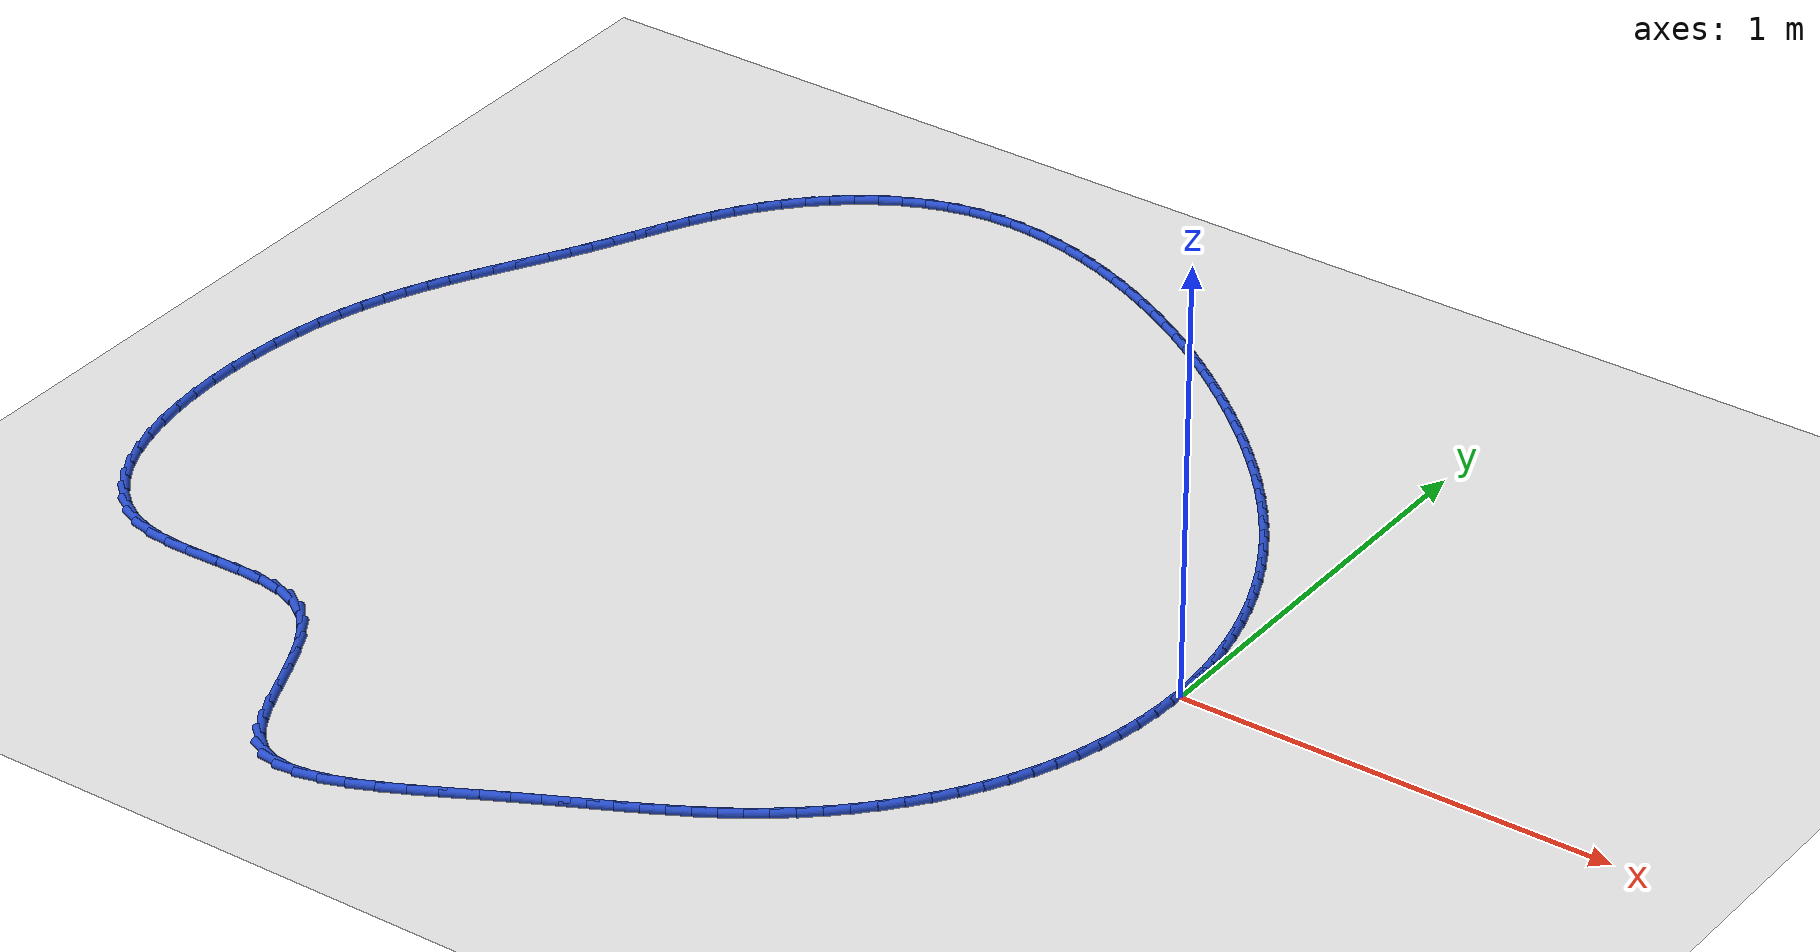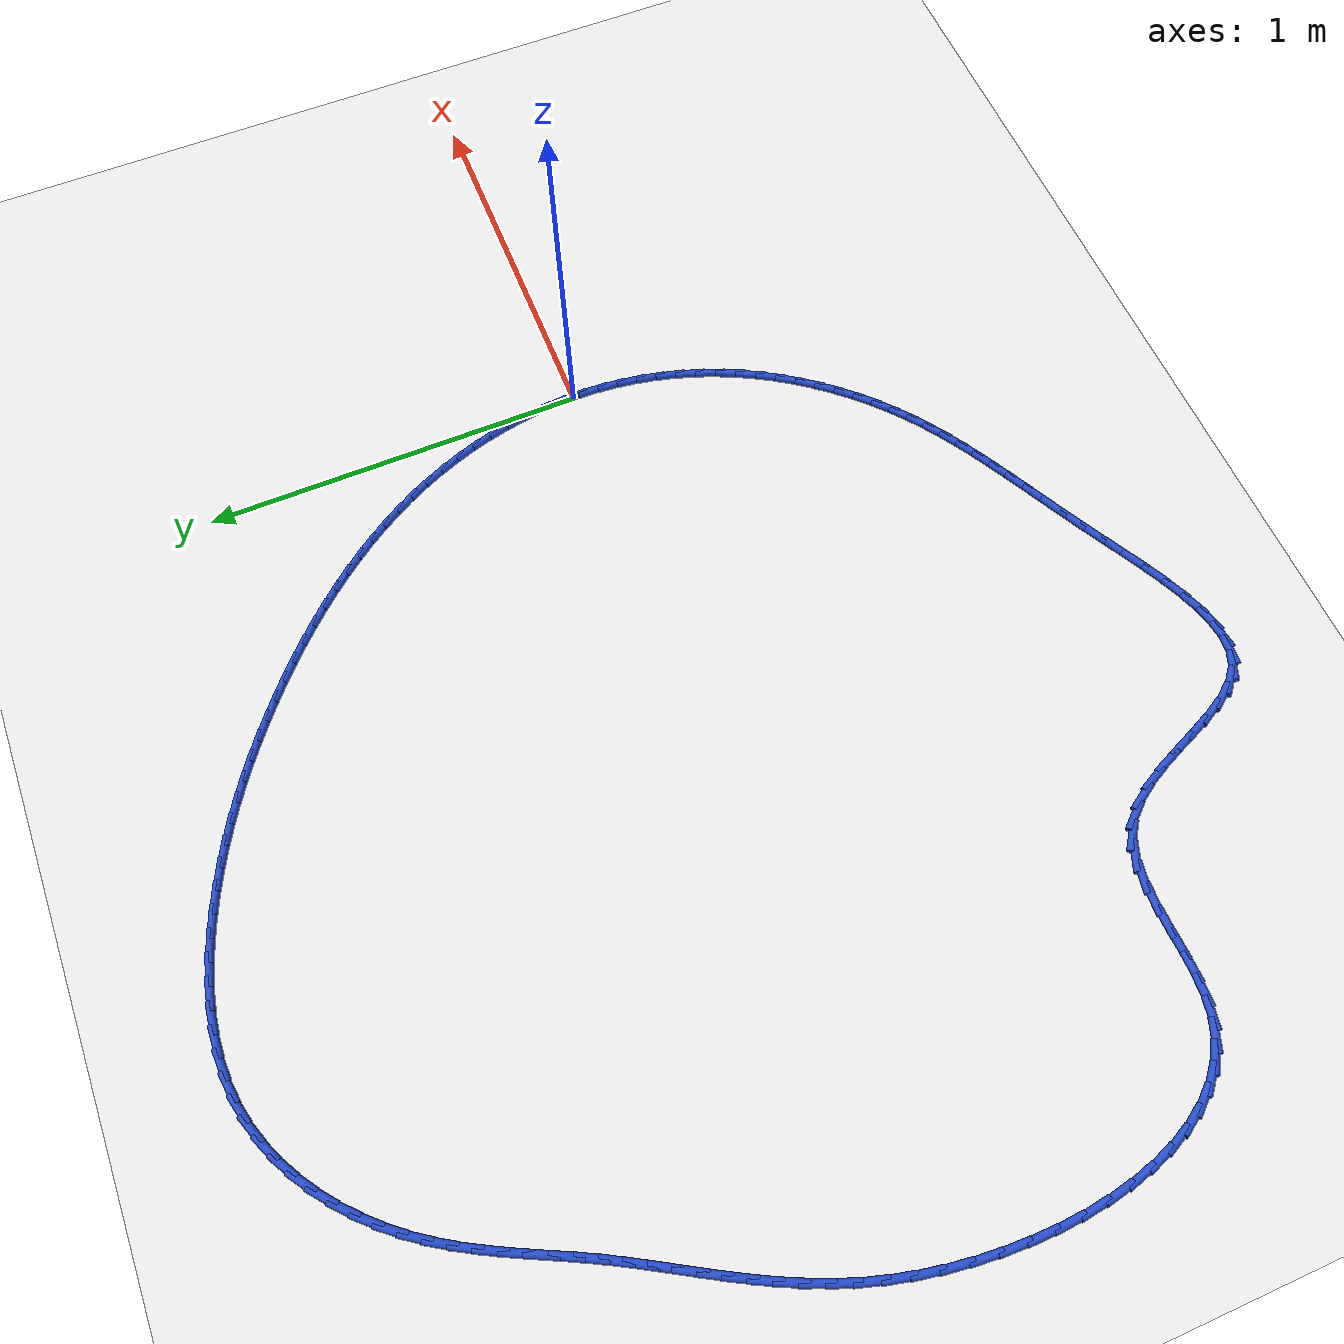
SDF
<sdf version="1.6">
 <world name="default">
  <light name="sun" type="directional">
   <pose>0 0 10 0 -0 0</pose>
   <diffuse>0.8 0.8 0.8 1</diffuse>
   <specular>0.2 0.2 0.2 1</specular>
   <attenuation>
    <range>1000</range>
    <constant>0.9</constant>
    <linear>0.01</linear>
    <quadratic>0.001</quadratic>
   </attenuation>
   <direction>-0.5 0.1 -0.9</direction>
  </light>
  <model name="ground_plane">
   <static>1</static>
   <link name="link">
    <collision name="collision">
     <geometry><plane><normal>0 0 1</normal><size>100 100</size></plane></geometry>
     <surface><friction><ode><mu>100</mu><mu2>50</mu2></ode></friction></surface>
    </collision>
    <visual name="visual">
     <cast_shadows>0</cast_shadows>
     <geometry><plane><normal>0 0 1</normal><size>100 100</size></plane></geometry>
     <material>
      <script><uri>file://media/materials/scripts/gazebo.material</uri><name>Gazebo/WhiteGlow</name></script>
     </material>
    </visual>
   </link>
  </model>
  <gravity>0 0 -9.8</gravity>
  <magnetic_field>6e-06 2.3e-05 -4.2e-05</magnetic_field>
  <atmosphere type="adiabatic"/>
  <physics name="default_physics" default="0" type="ode">
   <max_step_size>0.001</max_step_size>
   <real_time_factor>1</real_time_factor>
   <real_time_update_rate>1000</real_time_update_rate>
  </physics>
  <scene><ambient>0.4 0.4 0.4 1</ambient><background>0.7 0.7 0.7 1</background><shadows>1</shadows></scene>
  <spherical_coordinates>
   <surface_model>EARTH_WGS84</surface_model>
   <latitude_deg>0</latitude_deg>
   <longitude_deg>0</longitude_deg>
   <elevation>0</elevation>
   <heading_deg>0</heading_deg>
  </spherical_coordinates>
  <model name="line">
   <link name="link_0">
    <pose>-1.5612511283791264e-17 -1.6653345369377348e-16 0.01 0 1.57 -1.5351390074546476</pose>
    <collision name="collision">
     <geometry><cylinder><radius>0.01</radius><length>0.08</length></cylinder></geometry>
    </collision>
    <visual name="visual">
     <material>
      <script><name>Gazebo/Blue</name><uri>file://media/materials/scripts/gazebo.material</uri></script>
     </material>
     <geometry><cylinder><radius>0.01</radius><length>0.08</length></cylinder></geometry>
    </visual>
   </link>
   <link name="link_1">
    <pose>-0.0019127988193733663 0.053621195130851694 0.01 0 1.57 -1.4810969564794638</pose>
    <collision name="collision">
     <geometry><cylinder><radius>0.01</radius><length>0.08</length></cylinder></geometry>
    </collision>
    <visual name="visual">
     <material>
      <script><name>Gazebo/Blue</name><uri>file://media/materials/scripts/gazebo.material</uri></script>
     </material>
     <geometry><cylinder><radius>0.01</radius><length>0.08</length></cylinder></geometry>
    </visual>
   </link>
   <link name="link_2">
    <pose>-0.00672165869247289 0.1070881883489244 0.01 0 1.57 -1.4284923444065512</pose>
    <collision name="collision">
     <geometry><cylinder><radius>0.01</radius><length>0.08</length></cylinder></geometry>
    </collision>
    <visual name="visual">
     <material>
      <script><name>Gazebo/Blue</name><uri>file://media/materials/scripts/gazebo.material</uri></script>
     </material>
     <geometry><cylinder><radius>0.01</radius><length>0.08</length></cylinder></geometry>
    </visual>
   </link>
   <link name="link_3">
    <pose>-0.014341005209187739 0.16026902810462182 0.01 0 1.57 -1.377199438659335</pose>
    <collision name="collision">
     <geometry><cylinder><radius>0.01</radius><length>0.08</length></cylinder></geometry>
    </collision>
    <visual name="visual">
     <material>
      <script><name>Gazebo/Blue</name><uri>file://media/materials/scripts/gazebo.material</uri></script>
     </material>
     <geometry><cylinder><radius>0.01</radius><length>0.08</length></cylinder></geometry>
    </visual>
   </link>
   <link name="link_4">
    <pose>-0.024685263959407067 0.21303176284834768 0.01 0 1.57 -1.3270721663758944</pose>
    <collision name="collision">
     <geometry><cylinder><radius>0.01</radius><length>0.08</length></cylinder></geometry>
    </collision>
    <visual name="visual">
     <material>
      <script><name>Gazebo/Blue</name><uri>file://media/materials/scripts/gazebo.material</uri></script>
     </material>
     <geometry><cylinder><radius>0.01</radius><length>0.08</length></cylinder></geometry>
    </visual>
   </link>
   <link name="link_5">
    <pose>-0.03766886053302005 0.26524444103050576 0.01 0 1.57 -1.2779486032738683</pose>
    <collision name="collision">
     <geometry><cylinder><radius>0.01</radius><length>0.08</length></cylinder></geometry>
    </collision>
    <visual name="visual">
     <material>
      <script><name>Gazebo/Blue</name><uri>file://media/materials/scripts/gazebo.material</uri></script>
     </material>
     <geometry><cylinder><radius>0.01</radius><length>0.08</length></cylinder></geometry>
    </visual>
   </link>
   <link name="link_6">
    <pose>-0.05320622051991585 0.3167751111014999 0.01 0 1.57 -1.22965457174752</pose>
    <collision name="collision">
     <geometry><cylinder><radius>0.01</radius><length>0.08</length></cylinder></geometry>
    </collision>
    <visual name="visual">
     <material>
      <script><name>Gazebo/Blue</name><uri>file://media/materials/scripts/gazebo.material</uri></script>
     </material>
     <geometry><cylinder><radius>0.01</radius><length>0.08</length></cylinder></geometry>
    </visual>
   </link>
   <link name="link_7">
    <pose>-0.07121176950998365 0.367491821511734 0.01 0 1.57 -1.1820064087410085</pose>
    <collision name="collision">
     <geometry><cylinder><radius>0.01</radius><length>0.08</length></cylinder></geometry>
    </collision>
    <visual name="visual">
     <material>
      <script><name>Gazebo/Blue</name><uri>file://media/materials/scripts/gazebo.material</uri></script>
     </material>
     <geometry><cylinder><radius>0.01</radius><length>0.08</length></cylinder></geometry>
    </visual>
   </link>
   <link name="link_8">
    <pose>-0.09159993309311257 0.4172626207116117 0.01 0 1.57 -1.1348948468453819</pose>
    <collision name="collision">
     <geometry><cylinder><radius>0.01</radius><length>0.08</length></cylinder></geometry>
    </collision>
    <visual name="visual">
     <material>
      <script><name>Gazebo/Blue</name><uri>file://media/materials/scripts/gazebo.material</uri></script>
     </material>
     <geometry><cylinder><radius>0.01</radius><length>0.08</length></cylinder></geometry>
    </visual>
   </link>
   <link name="link_9">
    <pose>-0.11428325144515285 0.465961921098865 0.01 0 1.57 -1.0891571078992162</pose>
    <collision name="collision">
     <geometry><cylinder><radius>0.01</radius><length>0.08</length></cylinder></geometry>
    </collision>
    <visual name="visual">
     <material>
      <script><name>Gazebo/Blue</name><uri>file://media/materials/scripts/gazebo.material</uri></script>
     </material>
     <geometry><cylinder><radius>0.01</radius><length>0.08</length></cylinder></geometry>
    </visual>
   </link>
   <link name="link_10">
    <pose>-0.13915191184024098 0.5135395841164775 0.01 0 1.57 -1.04544608366425</pose>
    <collision name="collision">
     <geometry><cylinder><radius>0.01</radius><length>0.08</length></cylinder></geometry>
    </collision>
    <visual name="visual">
     <material>
      <script><name>Gazebo/Blue</name><uri>file://media/materials/scripts/gazebo.material</uri></script>
     </material>
     <geometry><cylinder><radius>0.01</radius><length>0.08</length></cylinder></geometry>
    </visual>
   </link>
   <link name="link_11">
    <pose>-0.1660814710647015 0.5599948543412692 0.01 0 1.57 -1.0037923445971124</pose>
    <collision name="collision">
     <geometry><cylinder><radius>0.01</radius><length>0.08</length></cylinder></geometry>
    </collision>
    <visual name="visual">
     <material>
      <script><name>Gazebo/Blue</name><uri>file://media/materials/scripts/gazebo.material</uri></script>
     </material>
     <geometry><cylinder><radius>0.01</radius><length>0.08</length></cylinder></geometry>
    </visual>
   </link>
   <link name="link_12">
    <pose>-0.19494723248706375 0.6053278317258375 0.01 0 1.57 -0.964185170395855</pose>
    <collision name="collision">
     <geometry><cylinder><radius>0.01</radius><length>0.08</length></cylinder></geometry>
    </collision>
    <visual name="visual">
     <material>
      <script><name>Gazebo/Blue</name><uri>file://media/materials/scripts/gazebo.material</uri></script>
     </material>
     <geometry><cylinder><radius>0.01</radius><length>0.08</length></cylinder></geometry>
    </visual>
   </link>
   <link name="link_13">
    <pose>-0.22562449947585717 0.6495386162227812 0.01 0 1.57 -0.9265892202288321</pose>
    <collision name="collision">
     <geometry><cylinder><radius>0.01</radius><length>0.08</length></cylinder></geometry>
    </collision>
    <visual name="visual">
     <material>
      <script><name>Gazebo/Blue</name><uri>file://media/materials/scripts/gazebo.material</uri></script>
     </material>
     <geometry><cylinder><radius>0.01</radius><length>0.08</length></cylinder></geometry>
    </visual>
   </link>
   <link name="link_14">
    <pose>-0.257988575399611 0.6926273077846979 0.01 0 1.57 -0.8909499251562601</pose>
    <collision name="collision">
     <geometry><cylinder><radius>0.01</radius><length>0.08</length></cylinder></geometry>
    </collision>
    <visual name="visual">
     <material>
      <script><name>Gazebo/Blue</name><uri>file://media/materials/scripts/gazebo.material</uri></script>
     </material>
     <geometry><cylinder><radius>0.01</radius><length>0.08</length></cylinder></geometry>
    </visual>
   </link>
   <link name="link_15">
    <pose>-0.2919147636268548 0.7345940063641859 0.01 0 1.57 -0.8571983679618527</pose>
    <collision name="collision">
     <geometry><cylinder><radius>0.01</radius><length>0.08</length></cylinder></geometry>
    </collision>
    <visual name="visual">
     <material>
      <script><name>Gazebo/Blue</name><uri>file://media/materials/scripts/gazebo.material</uri></script>
     </material>
     <geometry><cylinder><radius>0.01</radius><length>0.08</length></cylinder></geometry>
    </visual>
   </link>
   <link name="link_16">
    <pose>-0.327278367526118 0.775438811913843 0.01 0 1.57 -0.8252555261888134</pose>
    <collision name="collision">
     <geometry><cylinder><radius>0.01</radius><length>0.08</length></cylinder></geometry>
    </collision>
    <visual name="visual">
     <material>
      <script><name>Gazebo/Blue</name><uri>file://media/materials/scripts/gazebo.material</uri></script>
     </material>
     <geometry><cylinder><radius>0.01</radius><length>0.08</length></cylinder></geometry>
    </visual>
   </link>
   <link name="link_17">
    <pose>-0.3639546904659299 0.8151618243862675 0.01 0 1.57 -0.7950358378202791</pose>
    <collision name="collision">
     <geometry><cylinder><radius>0.01</radius><length>0.08</length></cylinder></geometry>
    </collision>
    <visual name="visual">
     <material>
      <script><name>Gazebo/Blue</name><uri>file://media/materials/scripts/gazebo.material</uri></script>
     </material>
     <geometry><cylinder><radius>0.01</radius><length>0.08</length></cylinder></geometry>
    </visual>
   </link>
   <link name="link_18">
    <pose>-0.4018190358148197 0.8537631437340569 0.01 0 1.57 -0.7664501071483063</pose>
    <collision name="collision">
     <geometry><cylinder><radius>0.01</radius><length>0.08</length></cylinder></geometry>
    </collision>
    <visual name="visual">
     <material>
      <script><name>Gazebo/Blue</name><uri>file://media/materials/scripts/gazebo.material</uri></script>
     </material>
     <geometry><cylinder><radius>0.01</radius><length>0.08</length></cylinder></geometry>
    </visual>
   </link>
   <link name="link_19">
    <pose>-0.4407467069413172 0.8912428699098098 0.01 0 1.57 -0.7394078043981044</pose>
    <collision name="collision">
     <geometry><cylinder><radius>0.01</radius><length>0.08</length></cylinder></geometry>
    </collision>
    <visual name="visual">
     <material>
      <script><name>Gazebo/Blue</name><uri>file://media/materials/scripts/gazebo.material</uri></script>
     </material>
     <geometry><cylinder><radius>0.01</radius><length>0.08</length></cylinder></geometry>
    </visual>
   </link>
   <link name="link_20">
    <pose>-0.4806130072139513 0.9276011028661236 0.01 0 1.57 -0.7138188314695952</pose>
    <collision name="collision">
     <geometry><cylinder><radius>0.01</radius><length>0.08</length></cylinder></geometry>
    </collision>
    <visual name="visual">
     <material>
      <script><name>Gazebo/Blue</name><uri>file://media/materials/scripts/gazebo.material</uri></script>
     </material>
     <geometry><cylinder><radius>0.01</radius><length>0.08</length></cylinder></geometry>
    </visual>
   </link>
   <link name="link_21">
    <pose>-0.5212932400012517 0.9628379425555968 0.01 0 1.57 -0.6895948326223554</pose>
    <collision name="collision">
     <geometry><cylinder><radius>0.01</radius><length>0.08</length></cylinder></geometry>
    </collision>
    <visual name="visual">
     <material>
      <script><name>Gazebo/Blue</name><uri>file://media/materials/scripts/gazebo.material</uri></script>
     </material>
     <geometry><cylinder><radius>0.01</radius><length>0.08</length></cylinder></geometry>
    </visual>
   </link>
   <link name="link_22">
    <pose>-0.5626627086717477 0.9969534889308276 0.01 0 1.57 -0.6664325448362454</pose>
    <collision name="collision">
     <geometry><cylinder><radius>0.01</radius><length>0.08</length></cylinder></geometry>
    </collision>
    <visual name="visual">
     <material>
      <script><name>Gazebo/Blue</name><uri>file://media/materials/scripts/gazebo.material</uri></script>
     </material>
     <geometry><cylinder><radius>0.01</radius><length>0.08</length></cylinder></geometry>
    </visual>
   </link>
   <link name="link_23">
    <pose>-0.604612770365231 1.0299456975328671 0.01 0 1.57 -0.6422736655266684</pose>
    <collision name="collision">
     <geometry><cylinder><radius>0.01</radius><length>0.08</length></cylinder></geometry>
    </collision>
    <visual name="visual">
     <material>
      <script><name>Gazebo/Blue</name><uri>file://media/materials/scripts/gazebo.material</uri></script>
     </material>
     <geometry><cylinder><radius>0.01</radius><length>0.08</length></cylinder></geometry>
    </visual>
   </link>
   <link name="link_24">
    <pose>-0.6471840494193232 1.0617925852667107 0.01 0 1.57 -0.6161100735033561</pose>
    <collision name="collision">
     <geometry><cylinder><radius>0.01</radius><length>0.08</length></cylinder></geometry>
    </collision>
    <visual name="visual">
     <material>
      <script><name>Gazebo/Blue</name><uri>file://media/materials/scripts/gazebo.material</uri></script>
     </material>
     <geometry><cylinder><radius>0.01</radius><length>0.08</length></cylinder></geometry>
    </visual>
   </link>
   <link name="link_25">
    <pose>-0.690498267277702 1.0924613363446625 0.01 0 1.57 -0.5880741647231125</pose>
    <collision name="collision">
     <geometry><cylinder><radius>0.01</radius><length>0.08</length></cylinder></geometry>
    </collision>
    <visual name="visual">
     <material>
      <script><name>Gazebo/Blue</name><uri>file://media/materials/scripts/gazebo.material</uri></script>
     </material>
     <geometry><cylinder><radius>0.01</radius><length>0.08</length></cylinder></geometry>
    </visual>
   </link>
   <link name="link_26">
    <pose>-0.734677953048937 1.1219190270937285 0.01 0 1.57 -0.5583430306676819</pose>
    <collision name="collision">
     <geometry><cylinder><radius>0.01</radius><length>0.08</length></cylinder></geometry>
    </collision>
    <visual name="visual">
     <material>
      <script><name>Gazebo/Blue</name><uri>file://media/materials/scripts/gazebo.material</uri></script>
     </material>
     <geometry><cylinder><radius>0.01</radius><length>0.08</length></cylinder></geometry>
    </visual>
   </link>
   <link name="link_27">
    <pose>-0.7798456358415969 1.150132733840913 0.01 0 1.57 -0.5271255613728094</pose>
    <collision name="collision">
     <geometry><cylinder><radius>0.01</radius><length>0.08</length></cylinder></geometry>
    </collision>
    <visual name="visual">
     <material>
      <script><name>Gazebo/Blue</name><uri>file://media/materials/scripts/gazebo.material</uri></script>
     </material>
     <geometry><cylinder><radius>0.01</radius><length>0.08</length></cylinder></geometry>
    </visual>
   </link>
   <link name="link_28">
    <pose>-0.826123844764251 1.1770695329132215 0.01 0 1.57 -0.49465869129787643</pose>
    <collision name="collision">
     <geometry><cylinder><radius>0.01</radius><length>0.08</length></cylinder></geometry>
    </collision>
    <visual name="visual">
     <material>
      <script><name>Gazebo/Blue</name><uri>file://media/materials/scripts/gazebo.material</uri></script>
     </material>
     <geometry><cylinder><radius>0.01</radius><length>0.08</length></cylinder></geometry>
    </visual>
   </link>
   <link name="link_29">
    <pose>-0.873635108925469 1.2026965006376595 0.01 0 1.57 -0.46119988137807816</pose>
    <collision name="collision">
     <geometry><cylinder><radius>0.01</radius><length>0.08</length></cylinder></geometry>
    </collision>
    <visual name="visual">
     <material>
      <script><name>Gazebo/Blue</name><uri>file://media/materials/scripts/gazebo.material</uri></script>
     </material>
     <geometry><cylinder><radius>0.01</radius><length>0.08</length></cylinder></geometry>
    </visual>
   </link>
   <link name="link_30">
    <pose>-0.9225017155278527 1.2269804712250076 0.01 0 1.57 -0.426180726905779</pose>
    <collision name="collision">
     <geometry><cylinder><radius>0.01</radius><length>0.08</length></cylinder></geometry>
    </collision>
    <visual name="visual">
     <material>
      <script><name>Gazebo/Blue</name><uri>file://media/materials/scripts/gazebo.material</uri></script>
     </material>
     <geometry><cylinder><radius>0.01</radius><length>0.08</length></cylinder></geometry>
    </visual>
   </link>
   <link name="link_31">
    <pose>-0.972752331127295 1.2497945768672378 0.01 0 1.57 -0.3873747355662771</pose>
    <collision name="collision">
     <geometry><cylinder><radius>0.01</radius><length>0.08</length></cylinder></geometry>
    </collision>
    <visual name="visual">
     <material>
      <script><name>Gazebo/Blue</name><uri>file://media/materials/scripts/gazebo.material</uri></script>
     </material>
     <geometry><cylinder><radius>0.01</radius><length>0.08</length></cylinder></geometry>
    </visual>
   </link>
   <link name="link_32">
    <pose>-1.0241806687030848 1.270776791965514 0.01 0 1.57 -0.34388318009219637</pose>
    <collision name="collision">
     <geometry><cylinder><radius>0.01</radius><length>0.08</length></cylinder></geometry>
    </collision>
    <visual name="visual">
     <material>
      <script><name>Gazebo/Blue</name><uri>file://media/materials/scripts/gazebo.material</uri></script>
     </material>
     <geometry><cylinder><radius>0.01</radius><length>0.08</length></cylinder></geometry>
    </visual>
   </link>
   <link name="link_33">
    <pose>-1.076544172377709 1.2895287905404553 0.01 0 1.57 -0.2950258008901564</pose>
    <collision name="collision">
     <geometry><cylinder><radius>0.01</radius><length>0.08</length></cylinder></geometry>
    </collision>
    <visual name="visual">
     <material>
      <script><name>Gazebo/Blue</name><uri>file://media/materials/scripts/gazebo.material</uri></script>
     </material>
     <geometry><cylinder><radius>0.01</radius><length>0.08</length></cylinder></geometry>
    </visual>
   </link>
   <link name="link_34">
    <pose>-1.1296002862736532 1.3056522466126814 0.01 0 1.57 -0.24004821847138225</pose>
    <collision name="collision">
     <geometry><cylinder><radius>0.01</radius><length>0.08</length></cylinder></geometry>
    </collision>
    <visual name="visual">
     <material>
      <script><name>Gazebo/Blue</name><uri>file://media/materials/scripts/gazebo.material</uri></script>
     </material>
     <geometry><cylinder><radius>0.01</radius><length>0.08</length></cylinder></geometry>
    </visual>
   </link>
   <link name="link_35">
    <pose>-1.183106454513405 1.3187488342028129 0.01 0 1.57 -0.17814583061397482</pose>
    <collision name="collision">
     <geometry><cylinder><radius>0.01</radius><length>0.08</length></cylinder></geometry>
    </collision>
    <visual name="visual">
     <material>
      <script><name>Gazebo/Blue</name><uri>file://media/materials/scripts/gazebo.material</uri></script>
     </material>
     <geometry><cylinder><radius>0.01</radius><length>0.08</length></cylinder></geometry>
    </visual>
   </link>
   <link name="link_36">
    <pose>-1.2368201212194503 1.3284202273314685 0.01 0 1.57 -0.10851438034527704</pose>
    <collision name="collision">
     <geometry><cylinder><radius>0.01</radius><length>0.08</length></cylinder></geometry>
    </collision>
    <visual name="visual">
     <material>
      <script><name>Gazebo/Blue</name><uri>file://media/materials/scripts/gazebo.material</uri></script>
     </material>
     <geometry><cylinder><radius>0.01</radius><length>0.08</length></cylinder></geometry>
    </visual>
   </link>
   <link name="link_37">
    <pose>-1.2904987305142765 1.3342681000192689 0.01 0 1.57 -0.0304399568864086</pose>
    <collision name="collision">
     <geometry><cylinder><radius>0.01</radius><length>0.08</length></cylinder></geometry>
    </collision>
    <visual name="visual">
     <material>
      <script><name>Gazebo/Blue</name><uri>file://media/materials/scripts/gazebo.material</uri></script>
     </material>
     <geometry><cylinder><radius>0.01</radius><length>0.08</length></cylinder></geometry>
    </visual>
   </link>
   <link name="link_38">
    <pose>-1.3438997265203696 1.3358941262868336 0.01 0 1.57 0.056560247076168094</pose>
    <collision name="collision">
     <geometry><cylinder><radius>0.01</radius><length>0.08</length></cylinder></geometry>
    </collision>
    <visual name="visual">
     <material>
      <script><name>Gazebo/Blue</name><uri>file://media/materials/scripts/gazebo.material</uri></script>
     </material>
     <geometry><cylinder><radius>0.01</radius><length>0.08</length></cylinder></geometry>
    </visual>
   </link>
   <link name="link_39">
    <pose>-1.396780553360217 1.3328999801547825 0.01 0 1.57 0.1525457686673668</pose>
    <collision name="collision">
     <geometry><cylinder><radius>0.01</radius><length>0.08</length></cylinder></geometry>
    </collision>
    <visual name="visual">
     <material>
      <script><name>Gazebo/Blue</name><uri>file://media/materials/scripts/gazebo.material</uri></script>
     </material>
     <geometry><cylinder><radius>0.01</radius><length>0.08</length></cylinder></geometry>
    </visual>
   </link>
   <link name="link_40">
    <pose>-1.4488986551563034 1.324887335643735 0.01 0 1.57 0.2562113360007099</pose>
    <collision name="collision">
     <geometry><cylinder><radius>0.01</radius><length>0.08</length></cylinder></geometry>
    </collision>
    <visual name="visual">
     <material>
      <script><name>Gazebo/Blue</name><uri>file://media/materials/scripts/gazebo.material</uri></script>
     </material>
     <geometry><cylinder><radius>0.01</radius><length>0.08</length></cylinder></geometry>
    </visual>
   </link>
   <link name="link_41">
    <pose>-1.5000110005244143 1.3114974943905264 0.01 0 1.57 0.3578988697251491</pose>
    <collision name="collision">
     <geometry><cylinder><radius>0.01</radius><length>0.08</length></cylinder></geometry>
    </collision>
    <visual name="visual">
     <material>
      <script><name>Gazebo/Blue</name><uri>file://media/materials/scripts/gazebo.material</uri></script>
     </material>
     <geometry><cylinder><radius>0.01</radius><length>0.08</length></cylinder></geometry>
    </visual>
   </link>
   <link name="link_42">
    <pose>-1.549868814959661 1.2928503762725883 0.01 0 1.57 0.45185800154394207</pose>
    <collision name="collision">
     <geometry><cylinder><radius>0.01</radius><length>0.08</length></cylinder></geometry>
    </collision>
    <visual name="visual">
     <material>
      <script><name>Gazebo/Blue</name><uri>file://media/materials/scripts/gazebo.material</uri></script>
     </material>
     <geometry><cylinder><radius>0.01</radius><length>0.08</length></cylinder></geometry>
    </visual>
   </link>
   <link name="link_43">
    <pose>-1.5982195138273476 1.269383428471747 0.01 0 1.57 0.5386670216102631</pose>
    <collision name="collision">
     <geometry><cylinder><radius>0.01</radius><length>0.08</length></cylinder></geometry>
    </collision>
    <visual name="visual">
     <material>
      <script><name>Gazebo/Blue</name><uri>file://media/materials/scripts/gazebo.material</uri></script>
     </material>
     <geometry><cylinder><radius>0.01</radius><length>0.08</length></cylinder></geometry>
    </visual>
   </link>
   <link name="link_44">
    <pose>-1.6448104441073668 1.2415397972500997 0.01 0 1.57 0.619288919932608</pose>
    <collision name="collision">
     <geometry><cylinder><radius>0.01</radius><length>0.08</length></cylinder></geometry>
    </collision>
    <visual name="visual">
     <material>
      <script><name>Gazebo/Blue</name><uri>file://media/materials/scripts/gazebo.material</uri></script>
     </material>
     <geometry><cylinder><radius>0.01</radius><length>0.08</length></cylinder></geometry>
    </visual>
   </link>
   <link name="link_45">
    <pose>-1.6893889527796087 1.2097626288697438 0.01 0 1.57 0.6948270344642553</pose>
    <collision name="collision">
     <geometry><cylinder><radius>0.01</radius><length>0.08</length></cylinder></geometry>
    </collision>
    <visual name="visual">
     <material>
      <script><name>Gazebo/Blue</name><uri>file://media/materials/scripts/gazebo.material</uri></script>
     </material>
     <geometry><cylinder><radius>0.01</radius><length>0.08</length></cylinder></geometry>
    </visual>
   </link>
   <link name="link_46">
    <pose>-1.7317023868239667 1.174495069592777 0.01 0 1.57 0.7664413663883005</pose>
    <collision name="collision">
     <geometry><cylinder><radius>0.01</radius><length>0.08</length></cylinder></geometry>
    </collision>
    <visual name="visual">
     <material>
      <script><name>Gazebo/Blue</name><uri>file://media/materials/scripts/gazebo.material</uri></script>
     </material>
     <geometry><cylinder><radius>0.01</radius><length>0.08</length></cylinder></geometry>
    </visual>
   </link>
   <link name="link_47">
    <pose>-1.7714980932203312 1.136180265681297 0.01 0 1.57 0.8353100413842313</pose>
    <collision name="collision">
     <geometry><cylinder><radius>0.01</radius><length>0.08</length></cylinder></geometry>
    </collision>
    <visual name="visual">
     <material>
      <script><name>Gazebo/Blue</name><uri>file://media/materials/scripts/gazebo.material</uri></script>
     </material>
     <geometry><cylinder><radius>0.01</radius><length>0.08</length></cylinder></geometry>
    </visual>
   </link>
   <link name="link_48">
    <pose>-1.8085234189485961 1.0952613633974007 0.01 0 1.57 0.9026230247563491</pose>
    <collision name="collision">
     <geometry><cylinder><radius>0.01</radius><length>0.08</length></cylinder></geometry>
    </collision>
    <visual name="visual">
     <material>
      <script><name>Gazebo/Blue</name><uri>file://media/materials/scripts/gazebo.material</uri></script>
     </material>
     <geometry><cylinder><radius>0.01</radius><length>0.08</length></cylinder></geometry>
    </visual>
   </link>
   <link name="link_49">
    <pose>-1.8425257109886508 1.0521815090031863 0.01 0 1.57 0.9679688689596162</pose>
    <collision name="collision">
     <geometry><cylinder><radius>0.01</radius><length>0.08</length></cylinder></geometry>
    </collision>
    <visual name="visual">
     <material>
      <script><name>Gazebo/Blue</name><uri>file://media/materials/scripts/gazebo.material</uri></script>
     </material>
     <geometry><cylinder><radius>0.01</radius><length>0.08</length></cylinder></geometry>
    </visual>
   </link>
   <link name="link_50">
    <pose>-1.8733649649941562 1.0073762686741925 0.01 0 1.57 1.0236584556788226</pose>
    <collision name="collision">
     <geometry><cylinder><radius>0.01</radius><length>0.08</length></cylinder></geometry>
    </collision>
    <visual name="visual">
     <material>
      <script><name>Gazebo/Blue</name><uri>file://media/materials/scripts/gazebo.material</uri></script>
     </material>
     <geometry><cylinder><radius>0.01</radius><length>0.08</length></cylinder></geometry>
    </visual>
   </link>
   <link name="link_51">
    <pose>-1.901468121589287 0.9612430590737892 0.01 0 1.57 1.0666442975080075</pose>
    <collision name="collision">
     <geometry><cylinder><radius>0.01</radius><length>0.08</length></cylinder></geometry>
    </collision>
    <visual name="visual">
     <material>
      <script><name>Gazebo/Blue</name><uri>file://media/materials/scripts/gazebo.material</uri></script>
     </material>
     <geometry><cylinder><radius>0.01</radius><length>0.08</length></cylinder></geometry>
    </visual>
   </link>
   <link name="link_52">
    <pose>-1.9274400867317472 0.9141673216455107 0.01 0 1.57 1.096635000104698</pose>
    <collision name="collision">
     <geometry><cylinder><radius>0.01</radius><length>0.08</length></cylinder></geometry>
    </collision>
    <visual name="visual">
     <material>
      <script><name>Gazebo/Blue</name><uri>file://media/materials/scripts/gazebo.material</uri></script>
     </material>
     <geometry><cylinder><radius>0.01</radius><length>0.08</length></cylinder></geometry>
    </visual>
   </link>
   <link name="link_53">
    <pose>-1.951885829891804 0.8665344935591558 0.01 0 1.57 1.1134902627350924</pose>
    <collision name="collision">
     <geometry><cylinder><radius>0.01</radius><length>0.08</length></cylinder></geometry>
    </collision>
    <visual name="visual">
     <material>
      <script><name>Gazebo/Blue</name><uri>file://media/materials/scripts/gazebo.material</uri></script>
     </material>
     <geometry><cylinder><radius>0.01</radius><length>0.08</length></cylinder></geometry>
    </visual>
   </link>
   <link name="link_54">
    <pose>-1.9754103205397266 0.8187300119845221 0.01 0 1.57 1.1170671915449875</pose>
    <collision name="collision">
     <geometry><cylinder><radius>0.01</radius><length>0.08</length></cylinder></geometry>
    </collision>
    <visual name="visual">
     <material>
      <script><name>Gazebo/Blue</name><uri>file://media/materials/scripts/gazebo.material</uri></script>
     </material>
     <geometry><cylinder><radius>0.01</radius><length>0.08</length></cylinder></geometry>
    </visual>
   </link>
   <link name="link_55">
    <pose>-1.9986185281457824 0.7711393140914072 0.01 0 1.57 1.1071290461043983</pose>
    <collision name="collision">
     <geometry><cylinder><radius>0.01</radius><length>0.08</length></cylinder></geometry>
    </collision>
    <visual name="visual">
     <material>
      <script><name>Gazebo/Blue</name><uri>file://media/materials/scripts/gazebo.material</uri></script>
     </material>
     <geometry><cylinder><radius>0.01</radius><length>0.08</length></cylinder></geometry>
    </visual>
   </link>
   <link name="link_56">
    <pose>-2.02211542218024 0.7241478370496097 0.01 0 1.57 1.0846794115029847</pose>
    <collision name="collision">
     <geometry><cylinder><radius>0.01</radius><length>0.08</length></cylinder></geometry>
    </collision>
    <visual name="visual">
     <material>
      <script><name>Gazebo/Blue</name><uri>file://media/materials/scripts/gazebo.material</uri></script>
     </material>
     <geometry><cylinder><radius>0.01</radius><length>0.08</length></cylinder></geometry>
    </visual>
   </link>
   <link name="link_57">
    <pose>-2.046449963591491 0.6780955028823921 0.01 0 1.57 1.062806701525071</pose>
    <collision name="collision">
     <geometry><cylinder><radius>0.01</radius><length>0.08</length></cylinder></geometry>
    </collision>
    <visual name="visual">
     <material>
      <script><name>Gazebo/Blue</name><uri>file://media/materials/scripts/gazebo.material</uri></script>
     </material>
     <geometry><cylinder><radius>0.01</radius><length>0.08</length></cylinder></geometry>
    </visual>
   </link>
   <link name="link_58">
    <pose>-2.0716238381366034 0.6328774921755836 0.01 0 1.57 1.0492954950425308</pose>
    <collision name="collision">
     <geometry><cylinder><radius>0.01</radius><length>0.08</length></cylinder></geometry>
    </collision>
    <visual name="visual">
     <material>
      <script><name>Gazebo/Blue</name><uri>file://media/materials/scripts/gazebo.material</uri></script>
     </material>
     <geometry><cylinder><radius>0.01</radius><length>0.08</length></cylinder></geometry>
    </visual>
   </link>
   <link name="link_59">
    <pose>-2.0973294166298495 0.5881376217140197 0.01 0 1.57 1.0444396385903945</pose>
    <collision name="collision">
     <geometry><cylinder><radius>0.01</radius><length>0.08</length></cylinder></geometry>
    </collision>
    <visual name="visual">
     <material>
      <script><name>Gazebo/Blue</name><uri>file://media/materials/scripts/gazebo.material</uri></script>
     </material>
     <geometry><cylinder><radius>0.01</radius><length>0.08</length></cylinder></geometry>
    </visual>
   </link>
   <link name="link_60">
    <pose>-2.123255566833727 0.5435168615386952 0.01 0 1.57 1.0482805100394543</pose>
    <collision name="collision">
     <geometry><cylinder><radius>0.01</radius><length>0.08</length></cylinder></geometry>
    </collision>
    <visual name="visual">
     <material>
      <script><name>Gazebo/Blue</name><uri>file://media/materials/scripts/gazebo.material</uri></script>
     </material>
     <geometry><cylinder><radius>0.01</radius><length>0.08</length></cylinder></geometry>
    </visual>
   </link>
   <link name="link_61">
    <pose>-2.1490911565107336 0.4986561816906031 0.01 0 1.57 1.060701548714605</pose>
    <collision name="collision">
     <geometry><cylinder><radius>0.01</radius><length>0.08</length></cylinder></geometry>
    </collision>
    <visual name="visual">
     <material>
      <script><name>Gazebo/Blue</name><uri>file://media/materials/scripts/gazebo.material</uri></script>
     </material>
     <geometry><cylinder><radius>0.01</radius><length>0.08</length></cylinder></geometry>
    </visual>
   </link>
   <link name="link_62">
    <pose>-2.174525053423368 0.45319655221073885 0.01 0 1.57 1.0814259967850304</pose>
    <collision name="collision">
     <geometry><cylinder><radius>0.01</radius><length>0.08</length></cylinder></geometry>
    </collision>
    <visual name="visual">
     <material>
      <script><name>Gazebo/Blue</name><uri>file://media/materials/scripts/gazebo.material</uri></script>
     </material>
     <geometry><cylinder><radius>0.01</radius><length>0.08</length></cylinder></geometry>
    </visual>
   </link>
   <link name="link_63">
    <pose>-2.1992461253341293 0.4067789431400957 0.01 0 1.57 1.1100051310889332</pose>
    <collision name="collision">
     <geometry><cylinder><radius>0.01</radius><length>0.08</length></cylinder></geometry>
    </collision>
    <visual name="visual">
     <material>
      <script><name>Gazebo/Blue</name><uri>file://media/materials/scripts/gazebo.material</uri></script>
     </material>
     <geometry><cylinder><radius>0.01</radius><length>0.08</length></cylinder></geometry>
    </visual>
   </link>
   <link name="link_64">
    <pose>-2.2229432400055145 0.35904432451966856 0.01 0 1.57 1.1458031505140482</pose>
    <collision name="collision">
     <geometry><cylinder><radius>0.01</radius><length>0.08</length></cylinder></geometry>
    </collision>
    <visual name="visual">
     <material>
      <script><name>Gazebo/Blue</name><uri>file://media/materials/scripts/gazebo.material</uri></script>
     </material>
     <geometry><cylinder><radius>0.01</radius><length>0.08</length></cylinder></geometry>
    </visual>
   </link>
   <link name="link_65">
    <pose>-2.245305265200024 0.3096336663904515 0.01 0 1.57 1.1879877986477299</pose>
    <collision name="collision">
     <geometry><cylinder><radius>0.01</radius><length>0.08</length></cylinder></geometry>
    </collision>
    <visual name="visual">
     <material>
      <script><name>Gazebo/Blue</name><uri>file://media/materials/scripts/gazebo.material</uri></script>
     </material>
     <geometry><cylinder><radius>0.01</radius><length>0.08</length></cylinder></geometry>
    </visual>
   </link>
   <link name="link_66">
    <pose>-2.2660210686801543 0.25818793879343815 0.01 0 1.57 1.2355367788353941</pose>
    <collision name="collision">
     <geometry><cylinder><radius>0.01</radius><length>0.08</length></cylinder></geometry>
    </collision>
    <visual name="visual">
     <material>
      <script><name>Gazebo/Blue</name><uri>file://media/materials/scripts/gazebo.material</uri></script>
     </material>
     <geometry><cylinder><radius>0.01</radius><length>0.08</length></cylinder></geometry>
    </visual>
   </link>
   <link name="link_67">
    <pose>-2.2847795182084045 0.20434811176962364 0.01 0 1.57 1.2872676983842066</pose>
    <collision name="collision">
     <geometry><cylinder><radius>0.01</radius><length>0.08</length></cylinder></geometry>
    </collision>
    <visual name="visual">
     <material>
      <script><name>Gazebo/Blue</name><uri>file://media/materials/scripts/gazebo.material</uri></script>
     </material>
     <geometry><cylinder><radius>0.01</radius><length>0.08</length></cylinder></geometry>
    </visual>
   </link>
   <link name="link_68">
    <pose>-2.301269486821531 0.14775518674799767 0.01 0 1.57 1.3406039720567804</pose>
    <collision name="collision">
     <geometry><cylinder><radius>0.01</radius><length>0.08</length></cylinder></geometry>
    </collision>
    <visual name="visual">
     <material>
      <script><name>Gazebo/Blue</name><uri>file://media/materials/scripts/gazebo.material</uri></script>
     </material>
     <geometry><cylinder><radius>0.01</radius><length>0.08</length></cylinder></geometry>
    </visual>
   </link>
   <link name="link_69">
    <pose>-2.3152137936498396 0.08825218409228722 0.01 0 1.57 1.3911987332797644</pose>
    <collision name="collision">
     <geometry><cylinder><radius>0.01</radius><length>0.08</length></cylinder></geometry>
    </collision>
    <visual name="visual">
     <material>
      <script><name>Gazebo/Blue</name><uri>file://media/materials/scripts/gazebo.material</uri></script>
     </material>
     <geometry><cylinder><radius>0.01</radius><length>0.08</length></cylinder></geometry>
    </visual>
   </link>
   <link name="link_70">
    <pose>-2.3264498334557264 0.026363983099624313 0.01 0 1.57 1.4396558018372605</pose>
    <collision name="collision">
     <geometry><cylinder><radius>0.01</radius><length>0.08</length></cylinder></geometry>
    </collision>
    <visual name="visual">
     <material>
      <script><name>Gazebo/Blue</name><uri>file://media/materials/scripts/gazebo.material</uri></script>
     </material>
     <geometry><cylinder><radius>0.01</radius><length>0.08</length></cylinder></geometry>
    </visual>
   </link>
   <link name="link_71">
    <pose>-2.3348391494016765 -0.03724082572631464 0.01 0 1.57 1.4874031911205035</pose>
    <collision name="collision">
     <geometry><cylinder><radius>0.01</radius><length>0.08</length></cylinder></geometry>
    </collision>
    <visual name="visual">
     <material>
      <script><name>Gazebo/Blue</name><uri>file://media/materials/scripts/gazebo.material</uri></script>
     </material>
     <geometry><cylinder><radius>0.01</radius><length>0.08</length></cylinder></geometry>
    </visual>
   </link>
   <link name="link_72">
    <pose>-2.340243284650177 -0.10189365188185462 0.01 0 1.57 1.535743510435168</pose>
    <collision name="collision">
     <geometry><cylinder><radius>0.01</radius><length>0.08</length></cylinder></geometry>
    </collision>
    <visual name="visual">
     <material>
      <script><name>Gazebo/Blue</name><uri>file://media/materials/scripts/gazebo.material</uri></script>
     </material>
     <geometry><cylinder><radius>0.01</radius><length>0.08</length></cylinder></geometry>
    </visual>
   </link>
   <link name="link_73">
    <pose>-2.34252378236371 -0.1669259048633213 0.01 0 1.57 -1.5556360762232304</pose>
    <collision name="collision">
     <geometry><cylinder><radius>0.01</radius><length>0.08</length></cylinder></geometry>
    </collision>
    <visual name="visual">
     <material>
      <script><name>Gazebo/Blue</name><uri>file://media/materials/scripts/gazebo.material</uri></script>
     </material>
     <geometry><cylinder><radius>0.01</radius><length>0.08</length></cylinder></geometry>
    </visual>
   </link>
   <link name="link_74">
    <pose>-2.3415421857047636 -0.23166899416703696 0.01 0 1.57 -1.5022026148852892</pose>
    <collision name="collision">
     <geometry><cylinder><radius>0.01</radius><length>0.08</length></cylinder></geometry>
    </collision>
    <visual name="visual">
     <material>
      <script><name>Gazebo/Blue</name><uri>file://media/materials/scripts/gazebo.material</uri></script>
     </material>
     <geometry><cylinder><radius>0.01</radius><length>0.08</length></cylinder></geometry>
    </visual>
   </link>
   <link name="link_75">
    <pose>-2.337160037835823 -0.2954543292893275 0.01 0 1.57 -1.4440457044604655</pose>
    <collision name="collision">
     <geometry><cylinder><radius>0.01</radius><length>0.08</length></cylinder></geometry>
    </collision>
    <visual name="visual">
     <material>
      <script><name>Gazebo/Blue</name><uri>file://media/materials/scripts/gazebo.material</uri></script>
     </material>
     <geometry><cylinder><radius>0.01</radius><length>0.08</length></cylinder></geometry>
    </visual>
   </link>
   <link name="link_76">
    <pose>-2.329238881919372 -0.35761331972651705 0.01 0 1.57 -1.3794181839525472</pose>
    <collision name="collision">
     <geometry><cylinder><radius>0.01</radius><length>0.08</length></cylinder></geometry>
    </collision>
    <visual name="visual">
     <material>
      <script><name>Gazebo/Blue</name><uri>file://media/materials/scripts/gazebo.material</uri></script>
     </material>
     <geometry><cylinder><radius>0.01</radius><length>0.08</length></cylinder></geometry>
    </visual>
   </link>
   <link name="link_77">
    <pose>-2.3176402611178966 -0.41747737497493054 0.01 0 1.57 -1.3062427389034317</pose>
    <collision name="collision">
     <geometry><cylinder><radius>0.01</radius><length>0.08</length></cylinder></geometry>
    </collision>
    <visual name="visual">
     <material>
      <script><name>Gazebo/Blue</name><uri>file://media/materials/scripts/gazebo.material</uri></script>
     </material>
     <geometry><cylinder><radius>0.01</radius><length>0.08</length></cylinder></geometry>
    </visual>
   </link>
   <link name="link_78">
    <pose>-2.302225718593882 -0.4743779045308931 0.01 0 1.57 -1.2220487191321432</pose>
    <collision name="collision">
     <geometry><cylinder><radius>0.01</radius><length>0.08</length></cylinder></geometry>
    </collision>
    <visual name="visual">
     <material>
      <script><name>Gazebo/Blue</name><uri>file://media/materials/scripts/gazebo.material</uri></script>
     </material>
     <geometry><cylinder><radius>0.01</radius><length>0.08</length></cylinder></geometry>
    </visual>
   </link>
   <link name="link_79">
    <pose>-2.2828567975098144 -0.5276463178907277 0.01 0 1.57 -1.1239860174097493</pose>
    <collision name="collision">
     <geometry><cylinder><radius>0.01</radius><length>0.08</length></cylinder></geometry>
    </collision>
    <visual name="visual">
     <material>
      <script><name>Gazebo/Blue</name><uri>file://media/materials/scripts/gazebo.material</uri></script>
     </material>
     <geometry><cylinder><radius>0.01</radius><length>0.08</length></cylinder></geometry>
    </visual>
   </link>
   <link name="link_80">
    <pose>-2.2593950410281782 -0.5766140245507598 0.01 0 1.57 -1.0090318992206129</pose>
    <collision name="collision">
     <geometry><cylinder><radius>0.01</radius><length>0.08</length></cylinder></geometry>
    </collision>
    <visual name="visual">
     <material>
      <script><name>Gazebo/Blue</name><uri>file://media/materials/scripts/gazebo.material</uri></script>
     </material>
     <geometry><cylinder><radius>0.01</radius><length>0.08</length></cylinder></geometry>
    </visual>
   </link>
   <link name="link_81">
    <pose>-2.2317019923114594 -0.6206124340073138 0.01 0 1.57 -0.8745875993310744</pose>
    <collision name="collision">
     <geometry><cylinder><radius>0.01</radius><length>0.08</length></cylinder></geometry>
    </collision>
    <visual name="visual">
     <material>
      <script><name>Gazebo/Blue</name><uri>file://media/materials/scripts/gazebo.material</uri></script>
     </material>
     <geometry><cylinder><radius>0.01</radius><length>0.08</length></cylinder></geometry>
    </visual>
   </link>
   <link name="link_82">
    <pose>-2.199639194522142 -0.6589729557567148 0.01 0 1.57 -0.7196721031065054</pose>
    <collision name="collision">
     <geometry><cylinder><radius>0.01</radius><length>0.08</length></cylinder></geometry>
    </collision>
    <visual name="visual">
     <material>
      <script><name>Gazebo/Blue</name><uri>file://media/materials/scripts/gazebo.material</uri></script>
     </material>
     <geometry><cylinder><radius>0.01</radius><length>0.08</length></cylinder></geometry>
    </visual>
   </link>
   <link name="link_83">
    <pose>-2.1630681908227127 -0.6910269992952861 0.01 0 1.57 -0.546611096932532</pose>
    <collision name="collision">
     <geometry><cylinder><radius>0.01</radius><length>0.08</length></cylinder></geometry>
    </collision>
    <visual name="visual">
     <material>
      <script><name>Gazebo/Blue</name><uri>file://media/materials/scripts/gazebo.material</uri></script>
     </material>
     <geometry><cylinder><radius>0.01</radius><length>0.08</length></cylinder></geometry>
    </visual>
   </link>
   <link name="link_84">
    <pose>-2.1218505243756574 -0.7161059741193533 0.01 0 1.57 -0.36227783582190964</pose>
    <collision name="collision">
     <geometry><cylinder><radius>0.01</radius><length>0.08</length></cylinder></geometry>
    </collision>
    <visual name="visual">
     <material>
      <script><name>Gazebo/Blue</name><uri>file://media/materials/scripts/gazebo.material</uri></script>
     </material>
     <geometry><cylinder><radius>0.01</radius><length>0.08</length></cylinder></geometry>
    </visual>
   </link>
   <link name="link_85">
    <pose>-2.0758477383434593 -0.7335412897252404 0.01 0 1.57 -0.18566326404982963</pose>
    <collision name="collision">
     <geometry><cylinder><radius>0.01</radius><length>0.08</length></cylinder></geometry>
    </collision>
    <visual name="visual">
     <material>
      <script><name>Gazebo/Blue</name><uri>file://media/materials/scripts/gazebo.material</uri></script>
     </material>
     <geometry><cylinder><radius>0.01</radius><length>0.08</length></cylinder></geometry>
    </visual>
   </link>
   <link name="link_86">
    <pose>-2.0251229717972463 -0.7430687409611028 0.01 0 1.57 -0.06281589172463498</pose>
    <collision name="collision">
     <geometry><cylinder><radius>0.01</radius><length>0.08</length></cylinder></geometry>
    </collision>
    <visual name="visual">
     <material>
      <script><name>Gazebo/Blue</name><uri>file://media/materials/scripts/gazebo.material</uri></script>
     </material>
     <geometry><cylinder><radius>0.01</radius><length>0.08</length></cylinder></geometry>
    </visual>
   </link>
   <link name="link_87">
    <pose>-1.9707680531151892 -0.746487591572637 0.01 0 1.57 0.004136916514954584</pose>
    <collision name="collision">
     <geometry><cylinder><radius>0.01</radius><length>0.08</length></cylinder></geometry>
    </collision>
    <visual name="visual">
     <material>
      <script><name>Gazebo/Blue</name><uri>file://media/materials/scripts/gazebo.material</uri></script>
     </material>
     <geometry><cylinder><radius>0.01</radius><length>0.08</length></cylinder></geometry>
    </visual>
   </link>
   <link name="link_88">
    <pose>-1.9142020799997166 -0.7462535815293142 0.01 0 1.57 0.02494096589458997</pose>
    <collision name="collision">
     <geometry><cylinder><radius>0.01</radius><length>0.08</length></cylinder></geometry>
    </collision>
    <visual name="visual">
     <material>
      <script><name>Gazebo/Blue</name><uri>file://media/materials/scripts/gazebo.material</uri></script>
     </material>
     <geometry><cylinder><radius>0.01</radius><length>0.08</length></cylinder></geometry>
    </visual>
   </link>
   <link name="link_89">
    <pose>-1.8568442873861757 -0.74482272607892 0.01 0 1.57 0.0030263342866266385</pose>
    <collision name="collision">
     <geometry><cylinder><radius>0.01</radius><length>0.08</length></cylinder></geometry>
    </collision>
    <visual name="visual">
     <material>
      <script><name>Gazebo/Blue</name><uri>file://media/materials/scripts/gazebo.material</uri></script>
     </material>
     <geometry><cylinder><radius>0.01</radius><length>0.08</length></cylinder></geometry>
    </visual>
   </link>
   <link name="link_90">
    <pose>-1.8001139102099122 -0.7446510404692389 0.01 0 1.57 -0.06470941897085686</pose>
    <collision name="collision">
     <geometry><cylinder><radius>0.01</radius><length>0.08</length></cylinder></geometry>
    </collision>
    <visual name="visual">
     <material>
      <script><name>Gazebo/Blue</name><uri>file://media/materials/scripts/gazebo.material</uri></script>
     </material>
     <geometry><cylinder><radius>0.01</radius><length>0.08</length></cylinder></geometry>
    </visual>
   </link>
   <link name="link_91">
    <pose>-1.745430183406272 -0.7481945399480567 0.01 0 1.57 -0.18744741719996655</pose>
    <collision name="collision">
     <geometry><cylinder><radius>0.01</radius><length>0.08</length></cylinder></geometry>
    </collision>
    <visual name="visual">
     <material>
      <script><name>Gazebo/Blue</name><uri>file://media/materials/scripts/gazebo.material</uri></script>
     </material>
     <geometry><cylinder><radius>0.01</radius><length>0.08</length></cylinder></geometry>
    </visual>
   </link>
   <link name="link_92">
    <pose>-1.694212341910603 -0.757909239763158 0.01 0 1.57 -0.37694434769025675</pose>
    <collision name="collision">
     <geometry><cylinder><radius>0.01</radius><length>0.08</length></cylinder></geometry>
    </collision>
    <visual name="visual">
     <material>
      <script><name>Gazebo/Blue</name><uri>file://media/materials/scripts/gazebo.material</uri></script>
     </material>
     <geometry><cylinder><radius>0.01</radius><length>0.08</length></cylinder></geometry>
    </visual>
   </link>
   <link name="link_93">
    <pose>-1.6478796206582516 -0.7762511551623287 0.01 0 1.57 -0.6296057664192739</pose>
    <collision name="collision">
     <geometry><cylinder><radius>0.01</radius><length>0.08</length></cylinder></geometry>
    </collision>
    <visual name="visual">
     <material>
      <script><name>Gazebo/Blue</name><uri>file://media/materials/scripts/gazebo.material</uri></script>
     </material>
     <geometry><cylinder><radius>0.01</radius><length>0.08</length></cylinder></geometry>
    </visual>
   </link>
   <link name="link_94">
    <pose>-1.6077490799376994 -0.805486699177137 0.01 0 1.57 -0.8602631397643337</pose>
    <collision name="collision">
     <geometry><cylinder><radius>0.01</radius><length>0.08</length></cylinder></geometry>
    </collision>
    <visual name="visual">
     <material>
      <script><name>Gazebo/Blue</name><uri>file://media/materials/scripts/gazebo.material</uri></script>
     </material>
     <geometry><cylinder><radius>0.01</radius><length>0.08</length></cylinder></geometry>
    </visual>
   </link>
   <link name="link_95">
    <pose>-1.5736481150785209 -0.8451179613372221 0.01 0 1.57 -1.0164147697314</pose>
    <collision name="collision">
     <geometry><cylinder><radius>0.01</radius><length>0.08</length></cylinder></geometry>
    </collision>
    <visual name="visual">
     <material>
      <script><name>Gazebo/Blue</name><uri>file://media/materials/scripts/gazebo.material</uri></script>
     </material>
     <geometry><cylinder><radius>0.01</radius><length>0.08</length></cylinder></geometry>
    </visual>
   </link>
   <link name="link_96">
    <pose>-1.5442770835854334 -0.8925556232162346 0.01 0 1.57 -1.1122242249419418</pose>
    <collision name="collision">
     <geometry><cylinder><radius>0.01</radius><length>0.08</length></cylinder></geometry>
    </collision>
    <visual name="visual">
     <material>
      <script><name>Gazebo/Blue</name><uri>file://media/materials/scripts/gazebo.material</uri></script>
     </material>
     <geometry><cylinder><radius>0.01</radius><length>0.08</length></cylinder></geometry>
    </visual>
   </link>
   <link name="link_97">
    <pose>-1.5183084675466254 -0.9451586388711282 0.01 0 1.57 -1.1618089078819454</pose>
    <collision name="collision">
     <geometry><cylinder><radius>0.01</radius><length>0.08</length></cylinder></geometry>
    </collision>
    <visual name="visual">
     <material>
      <script><name>Gazebo/Blue</name><uri>file://media/materials/scripts/gazebo.material</uri></script>
     </material>
     <geometry><cylinder><radius>0.01</radius><length>0.08</length></cylinder></geometry>
    </visual>
   </link>
   <link name="link_98">
    <pose>-1.4944147490502857 -1.0002859623588551 0.01 0 1.57 -1.172521159680965</pose>
    <collision name="collision">
     <geometry><cylinder><radius>0.01</radius><length>0.08</length></cylinder></geometry>
    </collision>
    <visual name="visual">
     <material>
      <script><name>Gazebo/Blue</name><uri>file://media/materials/scripts/gazebo.material</uri></script>
     </material>
     <geometry><cylinder><radius>0.01</radius><length>0.08</length></cylinder></geometry>
    </visual>
   </link>
   <link name="link_99">
    <pose>-1.471268410184602 -1.0552965477363678 0.01 0 1.57 -1.1445621893062383</pose>
    <collision name="collision">
     <geometry><cylinder><radius>0.01</radius><length>0.08</length></cylinder></geometry>
    </collision>
    <visual name="visual">
     <material>
      <script><name>Gazebo/Blue</name><uri>file://media/materials/scripts/gazebo.material</uri></script>
     </material>
     <geometry><cylinder><radius>0.01</radius><length>0.08</length></cylinder></geometry>
    </visual>
   </link>
   <link name="link_100">
    <pose>-1.4475419330377624 -1.1075493490606194 0.01 0 1.57 -1.0701769807290038</pose>
    <collision name="collision">
     <geometry><cylinder><radius>0.01</radius><length>0.08</length></cylinder></geometry>
    </collision>
    <visual name="visual">
     <material>
      <script><name>Gazebo/Blue</name><uri>file://media/materials/scripts/gazebo.material</uri></script>
     </material>
     <geometry><cylinder><radius>0.01</radius><length>0.08</length></cylinder></geometry>
    </visual>
   </link>
   <link name="link_101">
    <pose>-1.4219077996979548 -1.15440332038856 0.01 0 1.57 -0.9312852704834664</pose>
    <collision name="collision">
     <geometry><cylinder><radius>0.01</radius><length>0.08</length></cylinder></geometry>
    </collision>
    <visual name="visual">
     <material>
      <script><name>Gazebo/Blue</name><uri>file://media/materials/scripts/gazebo.material</uri></script>
     </material>
     <geometry><cylinder><radius>0.01</radius><length>0.08</length></cylinder></geometry>
    </visual>
   </link>
   <link name="link_102">
    <pose>-1.3930384922533683 -1.1932174157771438 0.01 0 1.57 -0.6995411871315361</pose>
    <collision name="collision">
     <geometry><cylinder><radius>0.01</radius><length>0.08</length></cylinder></geometry>
    </collision>
    <visual name="visual">
     <material>
      <script><name>Gazebo/Blue</name><uri>file://media/materials/scripts/gazebo.material</uri></script>
     </material>
     <geometry><cylinder><radius>0.01</radius><length>0.08</length></cylinder></geometry>
    </visual>
   </link>
   <link name="link_103">
    <pose>-1.3596064927921905 -1.2213505892833223 0.01 0 1.57 -0.37889989211413816</pose>
    <collision name="collision">
     <geometry><cylinder><radius>0.01</radius><length>0.08</length></cylinder></geometry>
    </collision>
    <visual name="visual">
     <material>
      <script><name>Gazebo/Blue</name><uri>file://media/materials/scripts/gazebo.material</uri></script>
     </material>
     <geometry><cylinder><radius>0.01</radius><length>0.08</length></cylinder></geometry>
    </visual>
   </link>
   <link name="link_104">
    <pose>-1.3206381715436069 -1.2368653460072616 0.01 0 1.57 -0.0873980718384954</pose>
    <collision name="collision">
     <geometry><cylinder><radius>0.01</radius><length>0.08</length></cylinder></geometry>
    </collision>
    <visual name="visual">
     <material>
      <script><name>Gazebo/Blue</name><uri>file://media/materials/scripts/gazebo.material</uri></script>
     </material>
     <geometry><cylinder><radius>0.01</radius><length>0.08</length></cylinder></geometry>
    </visual>
   </link>
   <link name="link_105">
    <pose>-1.2766177423717717 -1.2407224724307249 0.01 0 1.57 0.12572063078629084</pose>
    <collision name="collision">
     <geometry><cylinder><radius>0.01</radius><length>0.08</length></cylinder></geometry>
    </collision>
    <visual name="visual">
     <material>
      <script><name>Gazebo/Blue</name><uri>file://media/materials/scripts/gazebo.material</uri></script>
     </material>
     <geometry><cylinder><radius>0.01</radius><length>0.08</length></cylinder></geometry>
    </visual>
   </link>
   <link name="link_106">
    <pose>-1.2284047667826674 -1.2346289688651677 0.01 0 1.57 0.27128560058819773</pose>
    <collision name="collision">
     <geometry><cylinder><radius>0.01</radius><length>0.08</length></cylinder></geometry>
    </collision>
    <visual name="visual">
     <material>
      <script><name>Gazebo/Blue</name><uri>file://media/materials/scripts/gazebo.material</uri></script>
     </material>
     <geometry><cylinder><radius>0.01</radius><length>0.08</length></cylinder></geometry>
    </visual>
   </link>
   <link name="link_107">
    <pose>-1.1768588066266412 -1.2202918363066644 0.01 0 1.57 0.3687383506993966</pose>
    <collision name="collision">
     <geometry><cylinder><radius>0.01</radius><length>0.08</length></cylinder></geometry>
    </collision>
    <visual name="visual">
     <material>
      <script><name>Gazebo/Blue</name><uri>file://media/materials/scripts/gazebo.material</uri></script>
     </material>
     <geometry><cylinder><radius>0.01</radius><length>0.08</length></cylinder></geometry>
    </visual>
   </link>
   <link name="link_108">
    <pose>-1.1228394237540409 -1.1994180757512907 0.01 0 1.57 0.43280047578155767</pose>
    <collision name="collision">
     <geometry><cylinder><radius>0.01</radius><length>0.08</length></cylinder></geometry>
    </collision>
    <visual name="visual">
     <material>
      <script><name>Gazebo/Blue</name><uri>file://media/materials/scripts/gazebo.material</uri></script>
     </material>
     <geometry><cylinder><radius>0.01</radius><length>0.08</length></cylinder></geometry>
    </visual>
   </link>
   <link name="link_109">
    <pose>-1.067206180015214 -1.173714688195121 0.01 0 1.57 0.47257727667741417</pose>
    <collision name="collision">
     <geometry><cylinder><radius>0.01</radius><length>0.08</length></cylinder></geometry>
    </collision>
    <visual name="visual">
     <material>
      <script><name>Gazebo/Blue</name><uri>file://media/materials/scripts/gazebo.material</uri></script>
     </material>
     <geometry><cylinder><radius>0.01</radius><length>0.08</length></cylinder></geometry>
    </visual>
   </link>
   <link name="link_110">
    <pose>-1.0108186372605097 -1.1448886746342304 0.01 0 1.57 0.4930565986953674</pose>
    <collision name="collision">
     <geometry><cylinder><radius>0.01</radius><length>0.08</length></cylinder></geometry>
    </collision>
    <visual name="visual">
     <material>
      <script><name>Gazebo/Blue</name><uri>file://media/materials/scripts/gazebo.material</uri></script>
     </material>
     <geometry><cylinder><radius>0.01</radius><length>0.08</length></cylinder></geometry>
    </visual>
   </link>
   <link name="link_111">
    <pose>-0.954536357340276 -1.114647036064695 0.01 0 1.57 0.49623605324292946</pose>
    <collision name="collision">
     <geometry><cylinder><radius>0.01</radius><length>0.08</length></cylinder></geometry>
    </collision>
    <visual name="visual">
     <material>
      <script><name>Gazebo/Blue</name><uri>file://media/materials/scripts/gazebo.material</uri></script>
     </material>
     <geometry><cylinder><radius>0.01</radius><length>0.08</length></cylinder></geometry>
    </visual>
   </link>
   <link name="link_112">
    <pose>-0.8992189006969437 -1.0846967703425339 0.01 0 1.57 0.4856911034715962</pose>
    <collision name="collision">
     <geometry><cylinder><radius>0.01</radius><length>0.08</length></cylinder></geometry>
    </collision>
    <visual name="visual">
     <material>
      <script><name>Gazebo/Blue</name><uri>file://media/materials/scripts/gazebo.material</uri></script>
     </material>
     <geometry><cylinder><radius>0.01</radius><length>0.08</length></cylinder></geometry>
    </visual>
   </link>
   <link name="link_113">
    <pose>-0.8455582543475373 -1.0563711388503894 0.01 0 1.57 0.47591807990428736</pose>
    <collision name="collision">
     <geometry><cylinder><radius>0.01</radius><length>0.08</length></cylinder></geometry>
    </collision>
    <visual name="visual">
     <material>
      <script><name>Gazebo/Blue</name><uri>file://media/materials/scripts/gazebo.material</uri></script>
     </material>
     <geometry><cylinder><radius>0.01</radius><length>0.08</length></cylinder></geometry>
    </visual>
   </link>
   <link name="link_114">
    <pose>-0.7936165473674769 -1.029598640340709 0.01 0 1.57 0.4710391878446599</pose>
    <collision name="collision">
     <geometry><cylinder><radius>0.01</radius><length>0.08</length></cylinder></geometry>
    </collision>
    <visual name="visual">
     <material>
      <script><name>Gazebo/Blue</name><uri>file://media/materials/scripts/gazebo.material</uri></script>
     </material>
     <geometry><cylinder><radius>0.01</radius><length>0.08</length></cylinder></geometry>
    </visual>
   </link>
   <link name="link_115">
    <pose>-0.7433079503969073 -1.003977784108054 0.01 0 1.57 0.4716551694981317</pose>
    <collision name="collision">
     <geometry><cylinder><radius>0.01</radius><length>0.08</length></cylinder></geometry>
    </collision>
    <visual name="visual">
     <material>
      <script><name>Gazebo/Blue</name><uri>file://media/materials/scripts/gazebo.material</uri></script>
     </material>
     <geometry><cylinder><radius>0.01</radius><length>0.08</length></cylinder></geometry>
    </visual>
   </link>
   <link name="link_116">
    <pose>-0.6945466340759724 -0.9791070794469856 0.01 0 1.57 0.4782889114715015</pose>
    <collision name="collision">
     <geometry><cylinder><radius>0.01</radius><length>0.08</length></cylinder></geometry>
    </collision>
    <visual name="visual">
     <material>
      <script><name>Gazebo/Blue</name><uri>file://media/materials/scripts/gazebo.material</uri></script>
     </material>
     <geometry><cylinder><radius>0.01</radius><length>0.08</length></cylinder></geometry>
    </visual>
   </link>
   <link name="link_117">
    <pose>-0.6472467690448169 -0.9545850356520651 0.01 0 1.57 0.4913454807216737</pose>
    <collision name="collision">
     <geometry><cylinder><radius>0.01</radius><length>0.08</length></cylinder></geometry>
    </collision>
    <visual name="visual">
     <material>
      <script><name>Gazebo/Blue</name><uri>file://media/materials/scripts/gazebo.material</uri></script>
     </material>
     <geometry><cylinder><radius>0.01</radius><length>0.08</length></cylinder></geometry>
    </visual>
   </link>
   <link name="link_118">
    <pose>-0.6013225259435868 -0.9300101620178547 0.01 0 1.57 0.5110663511701681</pose>
    <collision name="collision">
     <geometry><cylinder><radius>0.01</radius><length>0.08</length></cylinder></geometry>
    </collision>
    <visual name="visual">
     <material>
      <script><name>Gazebo/Blue</name><uri>file://media/materials/scripts/gazebo.material</uri></script>
     </material>
     <geometry><cylinder><radius>0.01</radius><length>0.08</length></cylinder></geometry>
    </visual>
   </link>
   <link name="link_119">
    <pose>-0.5566880754124263 -0.9049809678389154 0.01 0 1.57 0.5374805232733235</pose>
    <collision name="collision">
     <geometry><cylinder><radius>0.01</radius><length>0.08</length></cylinder></geometry>
    </collision>
    <visual name="visual">
     <material>
      <script><name>Gazebo/Blue</name><uri>file://media/materials/scripts/gazebo.material</uri></script>
     </material>
     <geometry><cylinder><radius>0.01</radius><length>0.08</length></cylinder></geometry>
    </visual>
   </link>
   <link name="link_120">
    <pose>-0.5132575880914798 -0.8790959624098089 0.01 0 1.57 0.5703587265297233</pose>
    <collision name="collision">
     <geometry><cylinder><radius>0.01</radius><length>0.08</length></cylinder></geometry>
    </collision>
    <visual name="visual">
     <material>
      <script><name>Gazebo/Blue</name><uri>file://media/materials/scripts/gazebo.material</uri></script>
     </material>
     <geometry><cylinder><radius>0.01</radius><length>0.08</length></cylinder></geometry>
    </visual>
   </link>
   <link name="link_121">
    <pose>-0.47094523462089255 -0.8519536550250966 0.01 0 1.57 0.60918083256515</pose>
    <collision name="collision">
     <geometry><cylinder><radius>0.01</radius><length>0.08</length></cylinder></geometry>
    </collision>
    <visual name="visual">
     <material>
      <script><name>Gazebo/Blue</name><uri>file://media/materials/scripts/gazebo.material</uri></script>
     </material>
     <geometry><cylinder><radius>0.01</radius><length>0.08</length></cylinder></geometry>
    </visual>
   </link>
   <link name="link_122">
    <pose>-0.42966518564080847 -0.8231525549793393 0.01 0 1.57 0.6531291472372741</pose>
    <collision name="collision">
     <geometry><cylinder><radius>0.01</radius><length>0.08</length></cylinder></geometry>
    </collision>
    <visual name="visual">
     <material>
      <script><name>Gazebo/Blue</name><uri>file://media/materials/scripts/gazebo.material</uri></script>
     </material>
     <geometry><cylinder><radius>0.01</radius><length>0.08</length></cylinder></geometry>
    </visual>
   </link>
   <link name="link_123">
    <pose>-0.3893316117913738 -0.7922911715670998 0.01 0 1.57 0.7008997699939423</pose>
    <collision name="collision">
     <geometry><cylinder><radius>0.01</radius><length>0.08</length></cylinder></geometry>
    </collision>
    <visual name="visual">
     <material>
      <script><name>Gazebo/Blue</name><uri>file://media/materials/scripts/gazebo.material</uri></script>
     </material>
     <geometry><cylinder><radius>0.01</radius><length>0.08</length></cylinder></geometry>
    </visual>
   </link>
   <link name="link_124">
    <pose>-0.34987595111391895 -0.7589973937831261 0.01 0 1.57 0.74925995971805</pose>
    <collision name="collision">
     <geometry><cylinder><radius>0.01</radius><length>0.08</length></cylinder></geometry>
    </collision>
    <visual name="visual">
     <material>
      <script><name>Gazebo/Blue</name><uri>file://media/materials/scripts/gazebo.material</uri></script>
     </material>
     <geometry><cylinder><radius>0.01</radius><length>0.08</length></cylinder></geometry>
    </visual>
   </link>
   <link name="link_125">
    <pose>-0.3114227101890593 -0.7232276079877255 0.01 0 1.57 0.7970621373803342</pose>
    <collision name="collision">
     <geometry><cylinder><radius>0.01</radius><length>0.08</length></cylinder></geometry>
    </collision>
    <visual name="visual">
     <material>
      <script><name>Gazebo/Blue</name><uri>file://media/materials/scripts/gazebo.material</uri></script>
     </material>
     <geometry><cylinder><radius>0.01</radius><length>0.08</length></cylinder></geometry>
    </visual>
   </link>
   <link name="link_126">
    <pose>-0.2742174103351089 -0.6851441016303988 0.01 0 1.57 0.8448708888304121</pose>
    <collision name="collision">
     <geometry><cylinder><radius>0.01</radius><length>0.08</length></cylinder></geometry>
    </collision>
    <visual name="visual">
     <material>
      <script><name>Gazebo/Blue</name><uri>file://media/materials/scripts/gazebo.material</uri></script>
     </material>
     <geometry><cylinder><radius>0.01</radius><length>0.08</length></cylinder></geometry>
    </visual>
   </link>
   <link name="link_127">
    <pose>-0.23850743630759866 -0.6449123327145803 0.01 0 1.57 0.893236409134991</pose>
    <collision name="collision">
     <geometry><cylinder><radius>0.01</radius><length>0.08</length></cylinder></geometry>
    </collision>
    <visual name="visual">
     <material>
      <script><name>Gazebo/Blue</name><uri>file://media/materials/scripts/gazebo.material</uri></script>
     </material>
     <geometry><cylinder><radius>0.01</radius><length>0.08</length></cylinder></geometry>
    </visual>
   </link>
   <link name="link_128">
    <pose>-0.20454017286205786 -0.6026977592437011 0.01 0 1.57 0.9426843587966968</pose>
    <collision name="collision">
     <geometry><cylinder><radius>0.01</radius><length>0.08</length></cylinder></geometry>
    </collision>
    <visual name="visual">
     <material>
      <script><name>Gazebo/Blue</name><uri>file://media/materials/scripts/gazebo.material</uri></script>
     </material>
     <geometry><cylinder><radius>0.01</radius><length>0.08</length></cylinder></geometry>
    </visual>
   </link>
   <link name="link_129">
    <pose>-0.17256300475401606 -0.5586658392211941 0.01 0 1.57 0.9937256865172458</pose>
    <collision name="collision">
     <geometry><cylinder><radius>0.01</radius><length>0.08</length></cylinder></geometry>
    </collision>
    <visual name="visual">
     <material>
      <script><name>Gazebo/Blue</name><uri>file://media/materials/scripts/gazebo.material</uri></script>
     </material>
     <geometry><cylinder><radius>0.01</radius><length>0.08</length></cylinder></geometry>
    </visual>
   </link>
   <link name="link_130">
    <pose>-0.1428233167390032 -0.5129820306504912 0.01 0 1.57 1.0468625596953485</pose>
    <collision name="collision">
     <geometry><cylinder><radius>0.01</radius><length>0.08</length></cylinder></geometry>
    </collision>
    <visual name="visual">
     <material>
      <script><name>Gazebo/Blue</name><uri>file://media/materials/scripts/gazebo.material</uri></script>
     </material>
     <geometry><cylinder><radius>0.01</radius><length>0.08</length></cylinder></geometry>
    </visual>
   </link>
   <link name="link_131">
    <pose>-0.11556849357254848 -0.4658117915350242 0.01 0 1.57 1.1025655172053683</pose>
    <collision name="collision">
     <geometry><cylinder><radius>0.01</radius><length>0.08</length></cylinder></geometry>
    </collision>
    <visual name="visual">
     <material>
      <script><name>Gazebo/Blue</name><uri>file://media/materials/scripts/gazebo.material</uri></script>
     </material>
     <geometry><cylinder><radius>0.01</radius><length>0.08</length></cylinder></geometry>
    </visual>
   </link>
   <link name="link_132">
    <pose>-0.09104438420118248 -0.417320466542632 0.01 0 1.57 1.1598615592183295</pose>
    <collision name="collision">
     <geometry><cylinder><radius>0.01</radius><length>0.08</length></cylinder></geometry>
    </collision>
    <visual name="visual">
     <material>
      <script><name>Gazebo/Blue</name><uri>file://media/materials/scripts/gazebo.material</uri></script>
     </material>
     <geometry><cylinder><radius>0.01</radius><length>0.08</length></cylinder></geometry>
    </visual>
   </link>
   <link name="link_133">
    <pose>-0.06940817120590714 -0.3676668571738078 0.01 0 1.57 1.2167675048850948</pose>
    <collision name="collision">
     <geometry><cylinder><radius>0.01</radius><length>0.08</length></cylinder></geometry>
    </collision>
    <visual name="visual">
     <material>
      <script><name>Gazebo/Blue</name><uri>file://media/materials/scripts/gazebo.material</uri></script>
     </material>
     <geometry><cylinder><radius>0.01</radius><length>0.08</length></cylinder></geometry>
    </visual>
   </link>
   <link name="link_134">
    <pose>-0.05068157001314801 -0.3169997680801085 0.01 0 1.57 1.2731748757896428</pose>
    <collision name="collision">
     <geometry><cylinder><radius>0.01</radius><length>0.08</length></cylinder></geometry>
    </collision>
    <visual name="visual">
     <material>
      <script><name>Gazebo/Blue</name><uri>file://media/materials/scripts/gazebo.material</uri></script>
     </material>
     <geometry><cylinder><radius>0.01</radius><length>0.08</length></cylinder></geometry>
    </visual>
   </link>
   <link name="link_135">
    <pose>-0.03487486971737929 -0.26546716070268456 0.01 0 1.57 1.3291714121512581</pose>
    <collision name="collision">
     <geometry><cylinder><radius>0.01</radius><length>0.08</length></cylinder></geometry>
    </collision>
    <visual name="visual">
     <material>
      <script><name>Gazebo/Blue</name><uri>file://media/materials/scripts/gazebo.material</uri></script>
     </material>
     <geometry><cylinder><radius>0.01</radius><length>0.08</length></cylinder></geometry>
    </visual>
   </link>
   <link name="link_136">
    <pose>-0.02199835941307583 -0.21321699648268877 0.01 0 1.57 1.384857216397897</pose>
    <collision name="collision">
     <geometry><cylinder><radius>0.01</radius><length>0.08</length></cylinder></geometry>
    </collision>
    <visual name="visual">
     <material>
      <script><name>Gazebo/Blue</name><uri>file://media/materials/scripts/gazebo.material</uri></script>
     </material>
     <geometry><cylinder><radius>0.01</radius><length>0.08</length></cylinder></geometry>
    </visual>
   </link>
   <link name="link_137">
    <pose>-0.012062328194711786 -0.16039723686127136 0.01 0 1.57 1.4403415912827098</pose>
    <collision name="collision">
     <geometry><cylinder><radius>0.01</radius><length>0.08</length></cylinder></geometry>
    </collision>
    <visual name="visual">
     <material>
      <script><name>Gazebo/Blue</name><uri>file://media/materials/scripts/gazebo.material</uri></script>
     </material>
     <geometry><cylinder><radius>0.01</radius><length>0.08</length></cylinder></geometry>
    </visual>
   </link>
   <link name="link_138">
    <pose>-0.00507706515676153 -0.10715584327958348 0.01 0 1.57 1.495739964439206</pose>
    <collision name="collision">
     <geometry><cylinder><radius>0.01</radius><length>0.08</length></cylinder></geometry>
    </collision>
    <visual name="visual">
     <material>
      <script><name>Gazebo/Blue</name><uri>file://media/materials/scripts/gazebo.material</uri></script>
     </material>
     <geometry><cylinder><radius>0.01</radius><length>0.08</length></cylinder></geometry>
    </visual>
   </link>
   <link name="link_139">
    <pose>-0.0010528593936994773 -0.05364077717877629 0.01 0 1.57 1.5511708800147879</pose>
    <collision name="collision">
     <geometry><cylinder><radius>0.01</radius><length>0.08</length></cylinder></geometry>
    </collision>
    <visual name="visual">
     <material>
      <script><name>Gazebo/Blue</name><uri>file://media/materials/scripts/gazebo.material</uri></script>
     </material>
     <geometry><cylinder><radius>0.01</radius><length>0.08</length></cylinder></geometry>
    </visual>
   </link>
   <link name="link_140">
    <pose>-1.5612511283791264e-17 0.0 0.01 0 1.57 -1.5348396363495924</pose>
    <collision name="collision">
     <geometry><cylinder><radius>0.01</radius><length>0.08</length></cylinder></geometry>
    </collision>
    <visual name="visual">
     <material>
      <script><name>Gazebo/Blue</name><uri>file://media/materials/scripts/gazebo.material</uri></script>
     </material>
     <geometry><cylinder><radius>0.01</radius><length>0.08</length></cylinder></geometry>
    </visual>
   </link>
   <link name="link_141">
    <pose>-0.0019287760701375695 0.05361852681559252 0.01 0 1.57 -1.5348396363495926</pose>
    <collision name="collision">
     <geometry><cylinder><radius>0.01</radius><length>0.08</length></cylinder></geometry>
    </collision>
    <visual name="visual">
     <material>
      <script><name>Gazebo/Blue</name><uri>file://media/materials/scripts/gazebo.material</uri></script>
     </material>
     <geometry><cylinder><radius>0.01</radius><length>0.08</length></cylinder></geometry>
    </visual>
   </link>
  </model>
 </world>
</sdf>
